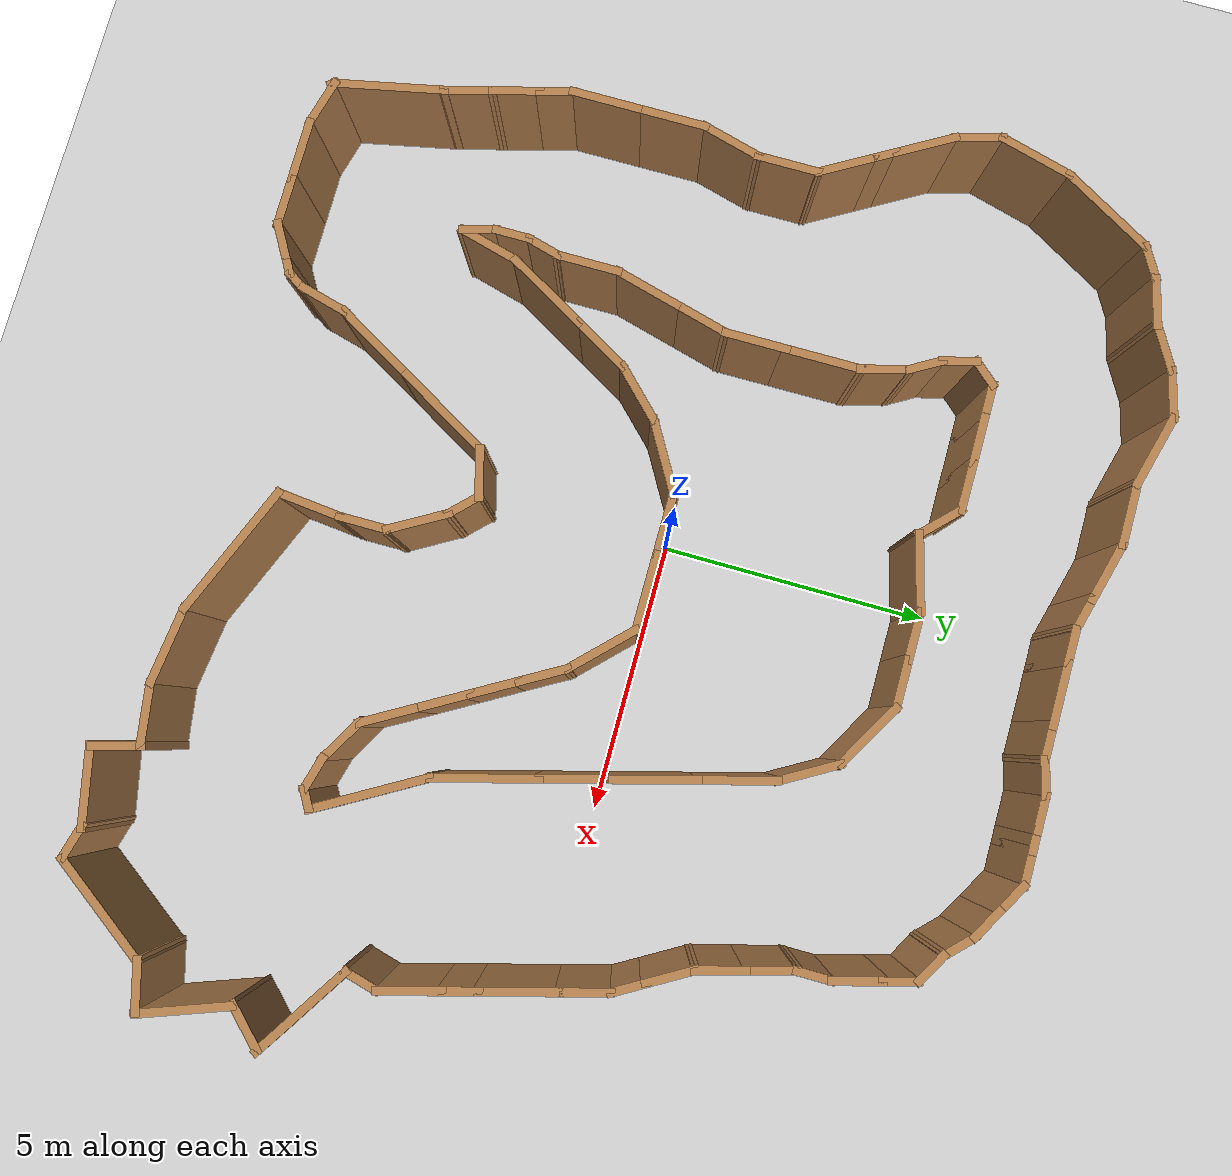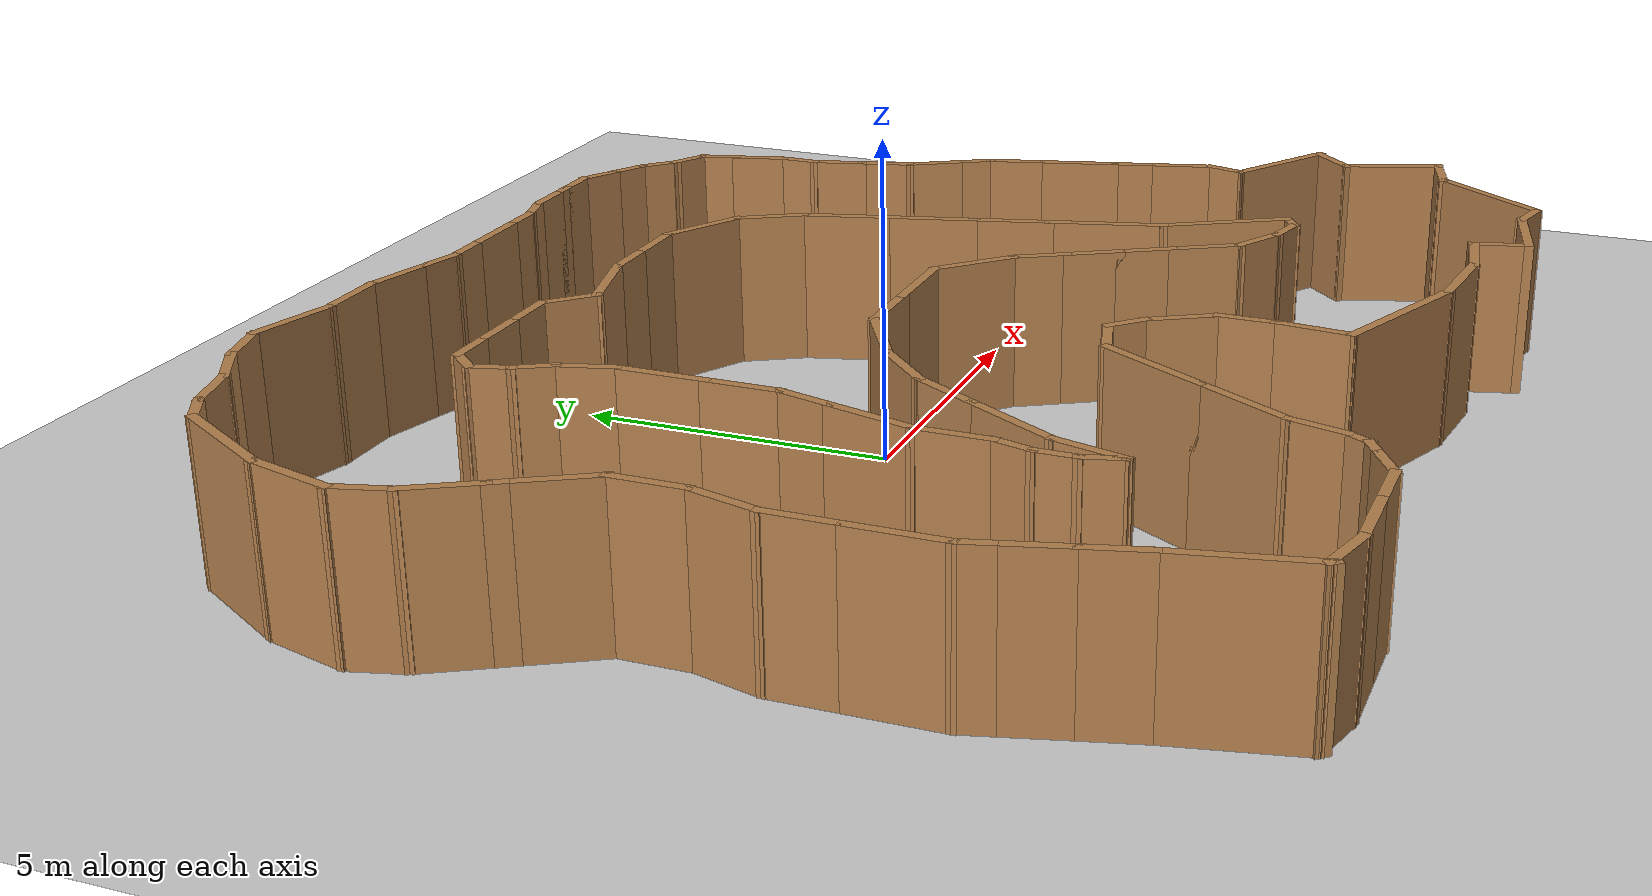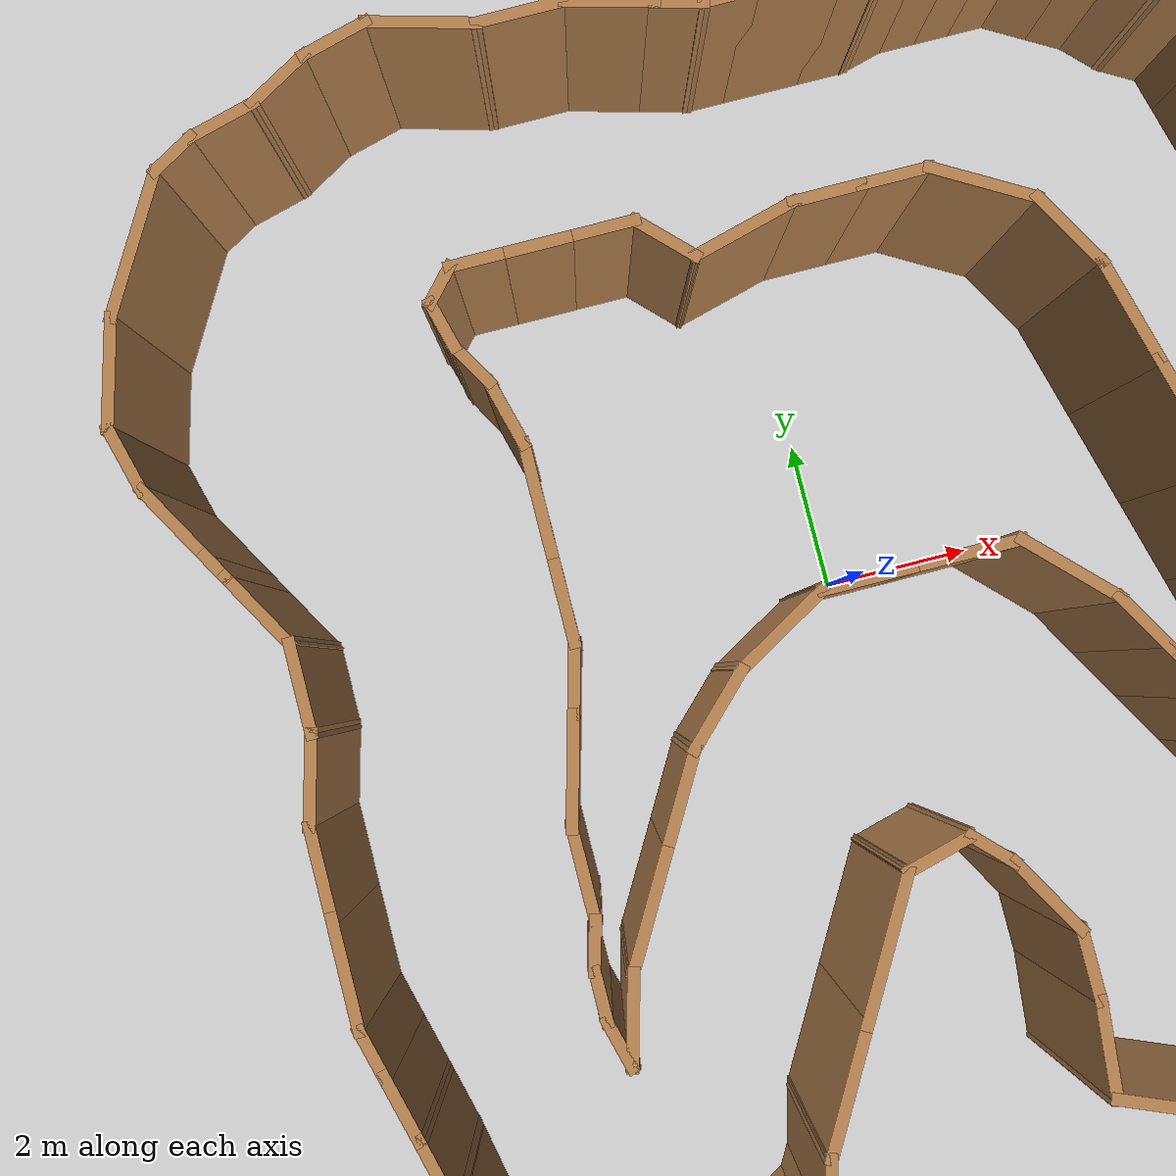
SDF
<sdf version="1.7">
 <world name="default">
  <light name="sun" type="directional">
   <pose>0 0 10 0 -0 0</pose>
   <diffuse>0.8 0.8 0.8 1</diffuse>
   <specular>0.2 0.2 0.2 1</specular>
   <attenuation>
    <range>1000</range>
    <constant>0.9</constant>
    <linear>0.01</linear>
    <quadratic>0.001</quadratic>
   </attenuation>
   <direction>-0.5 0.1 -0.9</direction>
   <spot><inner_angle>0</inner_angle><outer_angle>0</outer_angle><falloff>0</falloff></spot>
  </light>
  <model name="ground_plane">
   <static>1</static>
   <link name="link">
    <collision name="collision">
     <geometry><plane><normal>0 0 1</normal><size>100 100</size></plane></geometry>
     <surface><friction><ode><mu>100</mu><mu2>50</mu2></ode></friction></surface>
    </collision>
    <visual name="visual">
     <cast_shadows>0</cast_shadows>
     <geometry><plane><normal>0 0 1</normal><size>100 100</size></plane></geometry>
     <material>
      <script><uri>file://media/materials/scripts/gazebo.material</uri><name>Gazebo/Grey</name></script>
     </material>
    </visual>
   </link>
  </model>
  <gravity>0 0 -9.8</gravity>
  <magnetic_field>6e-06 2.3e-05 -4.2e-05</magnetic_field>
  <atmosphere type="adiabatic"/>
  <physics type="ode">
   <max_step_size>0.001</max_step_size>
   <real_time_factor>1</real_time_factor>
   <real_time_update_rate>1000</real_time_update_rate>
  </physics>
  <scene><ambient>0.4 0.4 0.4 1</ambient><background>0.7 0.7 0.7 1</background><shadows>1</shadows></scene>
  <audio><device>default</device></audio>
  <spherical_coordinates>
   <surface_model>EARTH_WGS84</surface_model>
   <latitude_deg>0</latitude_deg>
   <longitude_deg>0</longitude_deg>
   <elevation>0</elevation>
   <heading_deg>0</heading_deg>
  </spherical_coordinates>
  <model name="m-shape-circle">
   <pose>0.902463 -0.279625 0 0 -0 0</pose>
   <link name="Wall_10">
    <collision name="Wall_10_Collision">
     <geometry><box><size>0.75 0.15 2.5</size></box></geometry>
     <pose>0 0 1.25 0 -0 0</pose>
    </collision>
    <visual name="Wall_10_Visual">
     <pose>0 0 1.25 0 -0 0</pose>
     <geometry><box><size>0.75 0.15 2.5</size></box></geometry>
     <material>
      <script><uri>file://media/materials/scripts/gazebo.material</uri><name>Gazebo/Wood</name></script>
      <ambient>1 1 1 1</ambient>
     </material>
     <meta><layer>0</layer></meta>
    </visual>
    <pose>-8.04587 -3.77192 0 0 -0 1.8326</pose>
   </link>
   <link name="Wall_100">
    <collision name="Wall_100_Collision">
     <geometry><box><size>1 0.15 2.5</size></box></geometry>
     <pose>0 0 1.25 0 -0 0</pose>
    </collision>
    <visual name="Wall_100_Visual">
     <pose>0 0 1.25 0 -0 0</pose>
     <geometry><box><size>1 0.15 2.5</size></box></geometry>
     <material>
      <script><uri>file://media/materials/scripts/gazebo.material</uri><name>Gazebo/Wood</name></script>
      <ambient>1 1 1 1</ambient>
     </material>
     <meta><layer>0</layer></meta>
    </visual>
    <pose>0.581193 4.79872 0 0 -0 0</pose>
   </link>
   <link name="Wall_101">
    <collision name="Wall_101_Collision">
     <geometry><box><size>1.5 0.15 2.5</size></box></geometry>
     <pose>0 0 1.25 0 -0 0</pose>
    </collision>
    <visual name="Wall_101_Visual">
     <pose>0 0 1.25 0 -0 0</pose>
     <geometry><box><size>1.5 0.15 2.5</size></box></geometry>
     <material>
      <script><uri>file://media/materials/scripts/gazebo.material</uri><name>Gazebo/Wood</name></script>
      <ambient>1 1 1 1</ambient>
     </material>
     <meta><layer>0</layer></meta>
    </visual>
    <pose>1.59076 4.46122 0 0 -0 -0.523599</pose>
   </link>
   <link name="Wall_102">
    <collision name="Wall_102_Collision">
     <geometry><box><size>1.25 0.15 2.5</size></box></geometry>
     <pose>0 0 1.25 0 -0 0</pose>
    </collision>
    <visual name="Wall_102_Visual">
     <pose>0 0 1.25 0 -0 0</pose>
     <geometry><box><size>1.25 0.15 2.5</size></box></geometry>
     <material>
      <script><uri>file://media/materials/scripts/gazebo.material</uri><name>Gazebo/Wood</name></script>
      <ambient>1 1 1 1</ambient>
     </material>
     <meta><layer>0</layer></meta>
    </visual>
    <pose>2.45033 3.6474 0 0 -0 -1.0472</pose>
   </link>
   <link name="Wall_103">
    <collision name="Wall_103_Collision">
     <geometry><box><size>1.5 0.15 2.5</size></box></geometry>
     <pose>0 0 1.25 0 -0 0</pose>
    </collision>
    <visual name="Wall_103_Visual">
     <pose>0 0 1.25 0 -0 0</pose>
     <geometry><box><size>1.5 0.15 2.5</size></box></geometry>
     <material>
      <script><uri>file://media/materials/scripts/gazebo.material</uri><name>Gazebo/Wood</name></script>
      <ambient>1 1 1 1</ambient>
     </material>
     <meta><layer>0</layer></meta>
    </visual>
    <pose>2.90003 2.51909 0 0 -0 -1.309</pose>
   </link>
   <link name="Wall_104">
    <collision name="Wall_104_Collision">
     <geometry><box><size>1.75 0.15 2.5</size></box></geometry>
     <pose>0 0 1.25 0 -0 0</pose>
    </collision>
    <visual name="Wall_104_Visual">
     <pose>0 0 1.25 0 -0 0</pose>
     <geometry><box><size>1.75 0.15 2.5</size></box></geometry>
     <material>
      <script><uri>file://media/materials/scripts/gazebo.material</uri><name>Gazebo/Wood</name></script>
      <ambient>1 1 1 1</ambient>
     </material>
     <meta><layer>0</layer></meta>
    </visual>
    <pose>3.28179 1.09435 0 0 -0 -1.309</pose>
   </link>
   <link name="Wall_105">
    <collision name="Wall_105_Collision">
     <geometry><box><size>1.25 0.15 2.5</size></box></geometry>
     <pose>0 0 1.25 0 -0 0</pose>
    </collision>
    <visual name="Wall_105_Visual">
     <pose>0 0 1.25 0 -0 0</pose>
     <geometry><box><size>1.25 0.15 2.5</size></box></geometry>
     <material>
      <script><uri>file://media/materials/scripts/gazebo.material</uri><name>Gazebo/Wood</name></script>
      <ambient>1 1 1 1</ambient>
     </material>
     <meta><layer>0</layer></meta>
    </visual>
    <pose>3.63119 -0.209651 0 0 -0 -1.309</pose>
   </link>
   <link name="Wall_106">
    <collision name="Wall_106_Collision">
     <geometry><box><size>2 0.15 2.5</size></box></geometry>
     <pose>0 0 1.25 0 -0 0</pose>
    </collision>
    <visual name="Wall_106_Visual">
     <pose>0 0 1.25 0 -0 0</pose>
     <geometry><box><size>2 0.15 2.5</size></box></geometry>
     <material>
      <script><uri>file://media/materials/scripts/gazebo.material</uri><name>Gazebo/Wood</name></script>
      <ambient>1 1 1 1</ambient>
     </material>
     <meta><layer>0</layer></meta>
    </visual>
    <pose>4.01295 -1.63439 0 0 -0 -1.309</pose>
   </link>
   <link name="Wall_107">
    <collision name="Wall_107_Collision">
     <geometry><box><size>2.25 0.15 2.5</size></box></geometry>
     <pose>0 0 1.25 0 -0 0</pose>
    </collision>
    <visual name="Wall_107_Visual">
     <pose>0 0 1.25 0 -0 0</pose>
     <geometry><box><size>2.25 0.15 2.5</size></box></geometry>
     <material>
      <script><uri>file://media/materials/scripts/gazebo.material</uri><name>Gazebo/Wood</name></script>
      <ambient>1 1 1 1</ambient>
     </material>
     <meta><layer>0</layer></meta>
    </visual>
    <pose>4.77736 -3.4372 0 0 -0 -1.0472</pose>
   </link>
   <link name="Wall_108">
    <collision name="Wall_108_Collision">
     <geometry><box><size>0.5 0.15 2.5</size></box></geometry>
     <pose>0 0 1.25 0 -0 0</pose>
    </collision>
    <visual name="Wall_108_Visual">
     <pose>0 0 1.25 0 -0 0</pose>
     <geometry><box><size>0.5 0.15 2.5</size></box></geometry>
     <material>
      <script><uri>file://media/materials/scripts/gazebo.material</uri><name>Gazebo/Wood</name></script>
      <ambient>1 1 1 1</ambient>
     </material>
     <meta><layer>0</layer></meta>
    </visual>
    <pose>5.15081 -4.43403 0 0 -0 -2.61799</pose>
   </link>
   <link name="Wall_109">
    <collision name="Wall_109_Collision">
     <geometry><box><size>0.75 0.15 2.5</size></box></geometry>
     <pose>0 0 1.25 0 -0 0</pose>
    </collision>
    <visual name="Wall_109_Visual">
     <pose>0 0 1.25 0 -0 0</pose>
     <geometry><box><size>0.75 0.15 2.5</size></box></geometry>
     <material>
      <script><uri>file://media/materials/scripts/gazebo.material</uri><name>Gazebo/Wood</name></script>
      <ambient>1 1 1 1</ambient>
     </material>
     <meta><layer>0</layer></meta>
    </visual>
    <pose>4.70947 -4.44388 0 0 -0 2.87979</pose>
   </link>
   <link name="Wall_11">
    <collision name="Wall_11_Collision">
     <geometry><box><size>1.5 0.15 2.5</size></box></geometry>
     <pose>0 0 1.25 0 -0 0</pose>
    </collision>
    <visual name="Wall_11_Visual">
     <pose>0 0 1.25 0 -0 0</pose>
     <geometry><box><size>1.5 0.15 2.5</size></box></geometry>
     <material>
      <script><uri>file://media/materials/scripts/gazebo.material</uri><name>Gazebo/Wood</name></script>
      <ambient>1 1 1 1</ambient>
     </material>
     <meta><layer>0</layer></meta>
    </visual>
    <pose>-8.12351 -2.80714 0 0 -0 1.5708</pose>
   </link>
   <link name="Wall_110">
    <collision name="Wall_110_Collision">
     <geometry><box><size>1 0.15 2.5</size></box></geometry>
     <pose>0 0 1.25 0 -0 0</pose>
    </collision>
    <visual name="Wall_110_Visual">
     <pose>0 0 1.25 0 -0 0</pose>
     <geometry><box><size>1 0.15 2.5</size></box></geometry>
     <material>
      <script><uri>file://media/materials/scripts/gazebo.material</uri><name>Gazebo/Wood</name></script>
      <ambient>1 1 1 1</ambient>
     </material>
     <meta><layer>0</layer></meta>
    </visual>
    <pose>4.05163 -4.15374 0 0 -0 2.61799</pose>
   </link>
   <link name="Wall_111">
    <collision name="Wall_111_Collision">
     <geometry><box><size>1.25 0.15 2.5</size></box></geometry>
     <pose>0 0 1.25 0 -0 0</pose>
    </collision>
    <visual name="Wall_111_Visual">
     <pose>0 0 1.25 0 -0 0</pose>
     <geometry><box><size>1.25 0.15 2.5</size></box></geometry>
     <material>
      <script><uri>file://media/materials/scripts/gazebo.material</uri><name>Gazebo/Wood</name></script>
      <ambient>1 1 1 1</ambient>
     </material>
     <meta><layer>0</layer></meta>
    </visual>
    <pose>3.40857 -3.46492 0 0 -0 2.0944</pose>
   </link>
   <link name="Wall_112">
    <collision name="Wall_112_Collision">
     <geometry><box><size>1 0.15 2.5</size></box></geometry>
     <pose>0 0 1.25 0 -0 0</pose>
    </collision>
    <visual name="Wall_112_Visual">
     <pose>0 0 1.25 0 -0 0</pose>
     <geometry><box><size>1 0.15 2.5</size></box></geometry>
     <material>
      <script><uri>file://media/materials/scripts/gazebo.material</uri><name>Gazebo/Wood</name></script>
      <ambient>1 1 1 1</ambient>
     </material>
     <meta><layer>0</layer></meta>
    </visual>
    <pose>2.92107 -2.62055 0 0 -0 2.0944</pose>
   </link>
   <link name="Wall_113">
    <collision name="Wall_113_Collision">
     <geometry><box><size>1 0.15 2.5</size></box></geometry>
     <pose>0 0 1.25 0 -0 0</pose>
    </collision>
    <visual name="Wall_113_Visual">
     <pose>0 0 1.25 0 -0 0</pose>
     <geometry><box><size>1 0.15 2.5</size></box></geometry>
     <material>
      <script><uri>file://media/materials/scripts/gazebo.material</uri><name>Gazebo/Wood</name></script>
      <ambient>1 1 1 1</ambient>
     </material>
     <meta><layer>0</layer></meta>
    </visual>
    <pose>2.49607 -1.88443 0 0 -0 2.0944</pose>
   </link>
   <link name="Wall_114">
    <collision name="Wall_114_Collision">
     <geometry><box><size>1 0.15 2.5</size></box></geometry>
     <pose>0 0 1.25 0 -0 0</pose>
    </collision>
    <visual name="Wall_114_Visual">
     <pose>0 0 1.25 0 -0 0</pose>
     <geometry><box><size>1 0.15 2.5</size></box></geometry>
     <material>
      <script><uri>file://media/materials/scripts/gazebo.material</uri><name>Gazebo/Wood</name></script>
      <ambient>1 1 1 1</ambient>
     </material>
     <meta><layer>0</layer></meta>
    </visual>
    <pose>2.07107 -1.1483 0 0 -0 2.0944</pose>
   </link>
   <link name="Wall_115">
    <collision name="Wall_115_Collision">
     <geometry><box><size>1.5 0.15 2.5</size></box></geometry>
     <pose>0 0 1.25 0 -0 0</pose>
    </collision>
    <visual name="Wall_115_Visual">
     <pose>0 0 1.25 0 -0 0</pose>
     <geometry><box><size>1.5 0.15 2.5</size></box></geometry>
     <material>
      <script><uri>file://media/materials/scripts/gazebo.material</uri><name>Gazebo/Wood</name></script>
      <ambient>1 1 1 1</ambient>
     </material>
     <meta><layer>0</layer></meta>
    </visual>
    <pose>1.38128 -0.302945 0 0 -0 2.35619</pose>
   </link>
   <link name="Wall_116">
    <collision name="Wall_116_Collision">
     <geometry><box><size>1.5 0.15 2.5</size></box></geometry>
     <pose>0 0 1.25 0 -0 0</pose>
    </collision>
    <visual name="Wall_116_Visual">
     <pose>0 0 1.25 0 -0 0</pose>
     <geometry><box><size>1.5 0.15 2.5</size></box></geometry>
     <material>
      <script><uri>file://media/materials/scripts/gazebo.material</uri><name>Gazebo/Wood</name></script>
      <ambient>1 1 1 1</ambient>
     </material>
     <meta><layer>0</layer></meta>
    </visual>
    <pose>0.228979 0.174352 0 0 -0 3.14159</pose>
   </link>
   <link name="Wall_117">
    <collision name="Wall_117_Collision">
     <geometry><box><size>1.25 0.15 2.5</size></box></geometry>
     <pose>0 0 1.25 0 -0 0</pose>
    </collision>
    <visual name="Wall_117_Visual">
     <pose>0 0 1.25 0 -0 0</pose>
     <geometry><box><size>1.25 0.15 2.5</size></box></geometry>
     <material>
      <script><uri>file://media/materials/scripts/gazebo.material</uri><name>Gazebo/Wood</name></script>
      <ambient>1 1 1 1</ambient>
     </material>
     <meta><layer>0</layer></meta>
    </visual>
    <pose>-0.996021 0.174352 0 0 -0 3.14159</pose>
   </link>
   <link name="Wall_118">
    <collision name="Wall_118_Collision">
     <geometry><box><size>1.5 0.15 2.5</size></box></geometry>
     <pose>0 0 1.25 0 -0 0</pose>
    </collision>
    <visual name="Wall_118_Visual">
     <pose>0 0 1.25 0 -0 0</pose>
     <geometry><box><size>1.5 0.15 2.5</size></box></geometry>
     <material>
      <script><uri>file://media/materials/scripts/gazebo.material</uri><name>Gazebo/Wood</name></script>
      <ambient>1 1 1 1</ambient>
     </material>
     <meta><layer>0</layer></meta>
    </visual>
    <pose>-2.13059 -0.163148 0 0 -0 -2.61799</pose>
   </link>
   <link name="Wall_119">
    <collision name="Wall_119_Collision">
     <geometry><box><size>1.25 0.15 2.5</size></box></geometry>
     <pose>0 0 1.25 0 -0 0</pose>
    </collision>
    <visual name="Wall_119_Visual">
     <pose>0 0 1.25 0 -0 0</pose>
     <geometry><box><size>1.25 0.15 2.5</size></box></geometry>
     <material>
      <script><uri>file://media/materials/scripts/gazebo.material</uri><name>Gazebo/Wood</name></script>
      <ambient>1 1 1 1</ambient>
     </material>
     <meta><layer>0</layer></meta>
    </visual>
    <pose>-3.10406 -0.889557 0 0 -0 -2.35619</pose>
   </link>
   <link name="Wall_12">
    <collision name="Wall_12_Collision">
     <geometry><box><size>1.25 0.15 2.5</size></box></geometry>
     <pose>0 0 1.25 0 -0 0</pose>
    </collision>
    <visual name="Wall_12_Visual">
     <pose>0 0 1.25 0 -0 0</pose>
     <geometry><box><size>1.25 0.15 2.5</size></box></geometry>
     <material>
      <script><uri>file://media/materials/scripts/gazebo.material</uri><name>Gazebo/Wood</name></script>
      <ambient>1 1 1 1</ambient>
     </material>
     <meta><layer>0</layer></meta>
    </visual>
    <pose>-8.12351 -1.58214 0 0 -0 1.5708</pose>
   </link>
   <link name="Wall_120">
    <collision name="Wall_120_Collision">
     <geometry><box><size>1.25 0.15 2.5</size></box></geometry>
     <pose>0 0 1.25 0 -0 0</pose>
    </collision>
    <visual name="Wall_120_Visual">
     <pose>0 0 1.25 0 -0 0</pose>
     <geometry><box><size>1.25 0.15 2.5</size></box></geometry>
     <material>
      <script><uri>file://media/materials/scripts/gazebo.material</uri><name>Gazebo/Wood</name></script>
      <ambient>1 1 1 1</ambient>
     </material>
     <meta><layer>0</layer></meta>
    </visual>
    <pose>-3.76797 -1.75478 0 0 -0 -2.0944</pose>
   </link>
   <link name="Wall_121">
    <collision name="Wall_121_Collision">
     <geometry><box><size>1.75 0.15 2.5</size></box></geometry>
     <pose>0 0 1.25 0 -0 0</pose>
    </collision>
    <visual name="Wall_121_Visual">
     <pose>0 0 1.25 0 -0 0</pose>
     <geometry><box><size>1.75 0.15 2.5</size></box></geometry>
     <material>
      <script><uri>file://media/materials/scripts/gazebo.material</uri><name>Gazebo/Wood</name></script>
      <ambient>1 1 1 1</ambient>
     </material>
     <meta><layer>0</layer></meta>
    </visual>
    <pose>-4.44297 -2.92391 0 0 -0 -2.0944</pose>
   </link>
   <link name="Wall_122">
    <collision name="Wall_122_Collision">
     <geometry><box><size>1.25 0.15 2.5</size></box></geometry>
     <pose>0 0 1.25 0 -0 0</pose>
    </collision>
    <visual name="Wall_122_Visual">
     <pose>0 0 1.25 0 -0 0</pose>
     <geometry><box><size>1.25 0.15 2.5</size></box></geometry>
     <material>
      <script><uri>file://media/materials/scripts/gazebo.material</uri><name>Gazebo/Wood</name></script>
      <ambient>1 1 1 1</ambient>
     </material>
     <meta><layer>0</layer></meta>
    </visual>
    <pose>-4.98532 -4.14799 0 0 -0 -1.8326</pose>
   </link>
   <link name="Wall_123">
    <collision name="Wall_123_Collision">
     <geometry><box><size>0.75 0.15 2.5</size></box></geometry>
     <pose>0 0 1.25 0 -0 0</pose>
    </collision>
    <visual name="Wall_123_Visual">
     <pose>0 0 1.25 0 -0 0</pose>
     <geometry><box><size>0.75 0.15 2.5</size></box></geometry>
     <material>
      <script><uri>file://media/materials/scripts/gazebo.material</uri><name>Gazebo/Wood</name></script>
      <ambient>1 1 1 1</ambient>
     </material>
     <meta><layer>0</layer></meta>
    </visual>
    <pose>-5.20532 -4.38948 0 0 -0 1.8326</pose>
   </link>
   <link name="Wall_124">
    <collision name="Wall_124_Collision">
     <geometry><box><size>0.75 0.15 2.5</size></box></geometry>
     <pose>0 0 1.25 0 -0 0</pose>
    </collision>
    <visual name="Wall_124_Visual">
     <pose>0 0 1.25 0 -0 0</pose>
     <geometry><box><size>0.75 0.15 2.5</size></box></geometry>
     <material>
      <script><uri>file://media/materials/scripts/gazebo.material</uri><name>Gazebo/Wood</name></script>
      <ambient>1 1 1 1</ambient>
     </material>
     <meta><layer>0</layer></meta>
    </visual>
    <pose>-5.28296 -3.7997 0 0 -0 1.5708</pose>
   </link>
   <link name="Wall_125">
    <collision name="Wall_125_Collision">
     <geometry><box><size>0.75 0.15 2.5</size></box></geometry>
     <pose>0 0 1.25 0 -0 0</pose>
    </collision>
    <visual name="Wall_125_Visual">
     <pose>0 0 1.25 0 -0 0</pose>
     <geometry><box><size>0.75 0.15 2.5</size></box></geometry>
     <material>
      <script><uri>file://media/materials/scripts/gazebo.material</uri><name>Gazebo/Wood</name></script>
      <ambient>1 1 1 1</ambient>
     </material>
     <meta><layer>0</layer></meta>
    </visual>
    <pose>-5.20532 -3.20992 0 0 -0 1.309</pose>
   </link>
   <link name="Wall_126">
    <collision name="Wall_126_Collision">
     <geometry><box><size>1.25 0.15 2.5</size></box></geometry>
     <pose>0 0 1.25 0 -0 0</pose>
    </collision>
    <visual name="Wall_126_Visual">
     <pose>0 0 1.25 0 -0 0</pose>
     <geometry><box><size>1.25 0.15 2.5</size></box></geometry>
     <material>
      <script><uri>file://media/materials/scripts/gazebo.material</uri><name>Gazebo/Wood</name></script>
      <ambient>1 1 1 1</ambient>
     </material>
     <meta><layer>0</layer></meta>
    </visual>
    <pose>-5.12767 -2.37014 0 0 -0 1.5708</pose>
   </link>
   <link name="Wall_127">
    <collision name="Wall_127_Collision">
     <geometry><box><size>1.5 0.15 2.5</size></box></geometry>
     <pose>0 0 1.25 0 -0 0</pose>
    </collision>
    <visual name="Wall_127_Visual">
     <pose>0 0 1.25 0 -0 0</pose>
     <geometry><box><size>1.5 0.15 2.5</size></box></geometry>
     <material>
      <script><uri>file://media/materials/scripts/gazebo.material</uri><name>Gazebo/Wood</name></script>
      <ambient>1 1 1 1</ambient>
     </material>
     <meta><layer>0</layer></meta>
    </visual>
    <pose>-4.95297 -1.16814 0 0 -0 1.309</pose>
   </link>
   <link name="Wall_128">
    <collision name="Wall_128_Collision">
     <geometry><box><size>1 0.15 2.5</size></box></geometry>
     <pose>0 0 1.25 0 -0 0</pose>
    </collision>
    <visual name="Wall_128_Visual">
     <pose>0 0 1.25 0 -0 0</pose>
     <geometry><box><size>1 0.15 2.5</size></box></geometry>
     <material>
      <script><uri>file://media/materials/scripts/gazebo.material</uri><name>Gazebo/Wood</name></script>
      <ambient>1 1 1 1</ambient>
     </material>
     <meta><layer>0</layer></meta>
    </visual>
    <pose>-4.66827 -0.105623 0 0 -0 1.309</pose>
   </link>
   <link name="Wall_129">
    <collision name="Wall_129_Collision">
     <geometry><box><size>1.25 0.15 2.5</size></box></geometry>
     <pose>0 0 1.25 0 -0 0</pose>
    </collision>
    <visual name="Wall_129_Visual">
     <pose>0 0 1.25 0 -0 0</pose>
     <geometry><box><size>1.25 0.15 2.5</size></box></geometry>
     <material>
      <script><uri>file://media/materials/scripts/gazebo.material</uri><name>Gazebo/Wood</name></script>
      <ambient>1 1 1 1</ambient>
     </material>
     <meta><layer>0</layer></meta>
    </visual>
    <pose>-4.55827 0.854895 0 0 -0 1.5708</pose>
   </link>
   <link name="Wall_13">
    <collision name="Wall_13_Collision">
     <geometry><box><size>1.25 0.15 2.5</size></box></geometry>
     <pose>0 0 1.25 0 -0 0</pose>
    </collision>
    <visual name="Wall_13_Visual">
     <pose>0 0 1.25 0 -0 0</pose>
     <geometry><box><size>1.25 0.15 2.5</size></box></geometry>
     <material>
      <script><uri>file://media/materials/scripts/gazebo.material</uri><name>Gazebo/Wood</name></script>
      <ambient>1 1 1 1</ambient>
     </material>
     <meta><layer>0</layer></meta>
    </visual>
    <pose>-7.98116 -0.500884 0 0 -0 1.309</pose>
   </link>
   <link name="Wall_130">
    <collision name="Wall_130_Collision">
     <geometry><box><size>1.5 0.15 2.5</size></box></geometry>
     <pose>0 0 1.25 0 -0 0</pose>
    </collision>
    <visual name="Wall_130_Visual">
     <pose>0 0 1.25 0 -0 0</pose>
     <geometry><box><size>1.5 0.15 2.5</size></box></geometry>
     <material>
      <script><uri>file://media/materials/scripts/gazebo.material</uri><name>Gazebo/Wood</name></script>
      <ambient>1 1 1 1</ambient>
     </material>
     <meta><layer>0</layer></meta>
    </visual>
    <pose>-4.55827 2.0799 0 0 -0 1.5708</pose>
   </link>
   <link name="Wall_131">
    <collision name="Wall_131_Collision">
     <geometry><box><size>1 0.15 2.5</size></box></geometry>
     <pose>0 0 1.25 0 -0 0</pose>
    </collision>
    <visual name="Wall_131_Visual">
     <pose>0 0 1.25 0 -0 0</pose>
     <geometry><box><size>1 0.15 2.5</size></box></geometry>
     <material>
      <script><uri>file://media/materials/scripts/gazebo.material</uri><name>Gazebo/Wood</name></script>
      <ambient>1 1 1 1</ambient>
     </material>
     <meta><layer>0</layer></meta>
    </visual>
    <pose>-4.66827 3.16541 0 0 -0 1.8326</pose>
   </link>
   <link name="Wall_132">
    <collision name="Wall_132_Collision">
     <geometry><box><size>0.75 0.15 2.5</size></box></geometry>
     <pose>0 0 1.25 0 -0 0</pose>
    </collision>
    <visual name="Wall_132_Visual">
     <pose>0 0 1.25 0 -0 0</pose>
     <geometry><box><size>0.75 0.15 2.5</size></box></geometry>
     <material>
      <script><uri>file://media/materials/scripts/gazebo.material</uri><name>Gazebo/Wood</name></script>
      <ambient>1 1 1 1</ambient>
     </material>
     <meta><layer>0</layer></meta>
    </visual>
    <pose>-4.92827 3.83574 0 0 -0 2.0944</pose>
   </link>
   <link name="Wall_133">
    <collision name="Wall_133_Collision">
     <geometry><box><size>0.75 0.15 2.5</size></box></geometry>
     <pose>0 0 1.25 0 -0 0</pose>
    </collision>
    <visual name="Wall_133_Visual">
     <pose>0 0 1.25 0 -0 0</pose>
     <geometry><box><size>0.75 0.15 2.5</size></box></geometry>
     <material>
      <script><uri>file://media/materials/scripts/gazebo.material</uri><name>Gazebo/Wood</name></script>
      <ambient>1 1 1 1</ambient>
     </material>
     <meta><layer>0</layer></meta>
    </visual>
    <pose>-5.15591 4.38532 0 0 -0 1.8326</pose>
   </link>
   <link name="Wall_134">
    <collision name="Wall_134_Collision">
     <geometry><box><size>0.652836 0.15 2.5</size></box></geometry>
     <pose>0 0 1.25 0 -0 0</pose>
    </collision>
    <visual name="Wall_134_Visual">
     <pose>0 0 1.25 0 -0 0</pose>
     <geometry><box><size>0.652836 0.15 2.5</size></box></geometry>
     <material>
      <script><uri>file://media/materials/scripts/gazebo.material</uri><name>Gazebo/Wood</name></script>
      <ambient>1 1 1 1</ambient>
     </material>
     <meta><layer>0</layer></meta>
    </visual>
    <pose>-5.0662 4.86273 0 0 -0 0.842435</pose>
   </link>
   <link name="Wall_14">
    <collision name="Wall_14_Collision">
     <geometry><box><size>1.25 0.15 2.5</size></box></geometry>
     <pose>0 0 1.25 0 -0 0</pose>
    </collision>
    <visual name="Wall_14_Visual">
     <pose>0 0 1.25 0 -0 0</pose>
     <geometry><box><size>1.25 0.15 2.5</size></box></geometry>
     <material>
      <script><uri>file://media/materials/scripts/gazebo.material</uri><name>Gazebo/Wood</name></script>
      <ambient>1 1 1 1</ambient>
     </material>
     <meta><layer>0</layer></meta>
    </visual>
    <pose>-7.83881 0.580375 0 0 -0 1.5708</pose>
   </link>
   <link name="Wall_15">
    <collision name="Wall_15_Collision">
     <geometry><box><size>1.25 0.15 2.5</size></box></geometry>
     <pose>0 0 1.25 0 -0 0</pose>
    </collision>
    <visual name="Wall_15_Visual">
     <pose>0 0 1.25 0 -0 0</pose>
     <geometry><box><size>1.25 0.15 2.5</size></box></geometry>
     <material>
      <script><uri>file://media/materials/scripts/gazebo.material</uri><name>Gazebo/Wood</name></script>
      <ambient>1 1 1 1</ambient>
     </material>
     <meta><layer>0</layer></meta>
    </visual>
    <pose>-8.11381 1.60669 0 0 -0 2.0944</pose>
   </link>
   <link name="Wall_16">
    <collision name="Wall_16_Collision">
     <geometry><box><size>0.5 0.15 2.5</size></box></geometry>
     <pose>0 0 1.25 0 -0 0</pose>
    </collision>
    <visual name="Wall_16_Visual">
     <pose>0 0 1.25 0 -0 0</pose>
     <geometry><box><size>0.5 0.15 2.5</size></box></geometry>
     <material>
      <script><uri>file://media/materials/scripts/gazebo.material</uri><name>Gazebo/Wood</name></script>
      <ambient>1 1 1 1</ambient>
     </material>
     <meta><layer>0</layer></meta>
    </visual>
    <pose>-8.47631 2.23456 0 0 -0 2.0944</pose>
   </link>
   <link name="Wall_17">
    <collision name="Wall_17_Collision">
     <geometry><box><size>1.25 0.15 2.5</size></box></geometry>
     <pose>0 0 1.25 0 -0 0</pose>
    </collision>
    <visual name="Wall_17_Visual">
     <pose>0 0 1.25 0 -0 0</pose>
     <geometry><box><size>1.25 0.15 2.5</size></box></geometry>
     <material>
      <script><uri>file://media/materials/scripts/gazebo.material</uri><name>Gazebo/Wood</name></script>
      <ambient>1 1 1 1</ambient>
     </material>
     <meta><layer>0</layer></meta>
    </visual>
    <pose>-8.83881 2.86243 0 0 -0 2.0944</pose>
   </link>
   <link name="Wall_18">
    <collision name="Wall_18_Collision">
     <geometry><box><size>1 0.15 2.5</size></box></geometry>
     <pose>0 0 1.25 0 -0 0</pose>
    </collision>
    <visual name="Wall_18_Visual">
     <pose>0 0 1.25 0 -0 0</pose>
     <geometry><box><size>1 0.15 2.5</size></box></geometry>
     <material>
      <script><uri>file://media/materials/scripts/gazebo.material</uri><name>Gazebo/Wood</name></script>
      <ambient>1 1 1 1</ambient>
     </material>
     <meta><layer>0</layer></meta>
    </visual>
    <pose>-9.22381 3.74926 0 0 -0 1.8326</pose>
   </link>
   <link name="Wall_19">
    <collision name="Wall_19_Collision">
     <geometry><box><size>1.5 0.15 2.5</size></box></geometry>
     <pose>0 0 1.25 0 -0 0</pose>
    </collision>
    <visual name="Wall_19_Visual">
     <pose>0 0 1.25 0 -0 0</pose>
     <geometry><box><size>1.5 0.15 2.5</size></box></geometry>
     <material>
      <script><uri>file://media/materials/scripts/gazebo.material</uri><name>Gazebo/Wood</name></script>
      <ambient>1 1 1 1</ambient>
     </material>
     <meta><layer>0</layer></meta>
    </visual>
    <pose>-9.15911 4.81178 0 0 -0 1.309</pose>
   </link>
   <link name="Wall_20">
    <collision name="Wall_20_Collision">
     <geometry><box><size>2 0.15 2.5</size></box></geometry>
     <pose>0 0 1.25 0 -0 0</pose>
    </collision>
    <visual name="Wall_20_Visual">
     <pose>0 0 1.25 0 -0 0</pose>
     <geometry><box><size>2 0.15 2.5</size></box></geometry>
     <material>
      <script><uri>file://media/materials/scripts/gazebo.material</uri><name>Gazebo/Wood</name></script>
      <ambient>1 1 1 1</ambient>
     </material>
     <meta><layer>0</layer></meta>
    </visual>
    <pose>-8.5219 6.26485 0 0 -0 1.0472</pose>
   </link>
   <link name="Wall_21">
    <collision name="Wall_21_Collision">
     <geometry><box><size>0.75 0.15 2.5</size></box></geometry>
     <pose>0 0 1.25 0 -0 0</pose>
    </collision>
    <visual name="Wall_21_Visual">
     <pose>0 0 1.25 0 -0 0</pose>
     <geometry><box><size>0.75 0.15 2.5</size></box></geometry>
     <material>
      <script><uri>file://media/materials/scripts/gazebo.material</uri><name>Gazebo/Wood</name></script>
      <ambient>1 1 1 1</ambient>
     </material>
     <meta><layer>0</layer></meta>
    </visual>
    <pose>-7.7996 7.21592 0 0 -0 0.523599</pose>
   </link>
   <link name="Wall_22">
    <collision name="Wall_22_Collision">
     <geometry><box><size>1 0.15 2.5</size></box></geometry>
     <pose>0 0 1.25 0 -0 0</pose>
    </collision>
    <visual name="Wall_22_Visual">
     <pose>0 0 1.25 0 -0 0</pose>
     <geometry><box><size>1 0.15 2.5</size></box></geometry>
     <material>
      <script><uri>file://media/materials/scripts/gazebo.material</uri><name>Gazebo/Wood</name></script>
      <ambient>1 1 1 1</ambient>
     </material>
     <meta><layer>0</layer></meta>
    </visual>
    <pose>-7.12927 7.47592 0 0 -0 0.261799</pose>
   </link>
   <link name="Wall_23">
    <collision name="Wall_23_Collision">
     <geometry><box><size>1 0.15 2.5</size></box></geometry>
     <pose>0 0 1.25 0 -0 0</pose>
    </collision>
    <visual name="Wall_23_Visual">
     <pose>0 0 1.25 0 -0 0</pose>
     <geometry><box><size>1 0.15 2.5</size></box></geometry>
     <material>
      <script><uri>file://media/materials/scripts/gazebo.material</uri><name>Gazebo/Wood</name></script>
      <ambient>1 1 1 1</ambient>
     </material>
     <meta><layer>0</layer></meta>
    </visual>
    <pose>-6.35069 7.79842 0 0 -0 0.523599</pose>
   </link>
   <link name="Wall_24">
    <collision name="Wall_24_Collision">
     <geometry><box><size>1 0.15 2.5</size></box></geometry>
     <pose>0 0 1.25 0 -0 0</pose>
    </collision>
    <visual name="Wall_24_Visual">
     <pose>0 0 1.25 0 -0 0</pose>
     <geometry><box><size>1 0.15 2.5</size></box></geometry>
     <material>
      <script><uri>file://media/materials/scripts/gazebo.material</uri><name>Gazebo/Wood</name></script>
      <ambient>1 1 1 1</ambient>
     </material>
     <meta><layer>0</layer></meta>
    </visual>
    <pose>-5.57211 8.12092 0 0 -0 0.261799</pose>
   </link>
   <link name="Wall_25">
    <collision name="Wall_25_Collision">
     <geometry><box><size>1.5 0.15 2.5</size></box></geometry>
     <pose>0 0 1.25 0 -0 0</pose>
    </collision>
    <visual name="Wall_25_Visual">
     <pose>0 0 1.25 0 -0 0</pose>
     <geometry><box><size>1.5 0.15 2.5</size></box></geometry>
     <material>
      <script><uri>file://media/materials/scripts/gazebo.material</uri><name>Gazebo/Wood</name></script>
      <ambient>1 1 1 1</ambient>
     </material>
     <meta><layer>0</layer></meta>
    </visual>
    <pose>-4.50959 8.05621 0 0 -0 -0.261799</pose>
   </link>
   <link name="Wall_26">
    <collision name="Wall_26_Collision">
     <geometry><box><size>1.25 0.15 2.5</size></box></geometry>
     <pose>0 0 1.25 0 -0 0</pose>
    </collision>
    <visual name="Wall_26_Visual">
     <pose>0 0 1.25 0 -0 0</pose>
     <geometry><box><size>1.25 0.15 2.5</size></box></geometry>
     <material>
      <script><uri>file://media/materials/scripts/gazebo.material</uri><name>Gazebo/Wood</name></script>
      <ambient>1 1 1 1</ambient>
     </material>
     <meta><layer>0</layer></meta>
    </visual>
    <pose>-3.30759 7.88151 0 0 -0 0</pose>
   </link>
   <link name="Wall_27">
    <collision name="Wall_27_Collision">
     <geometry><box><size>1.25 0.15 2.5</size></box></geometry>
     <pose>0 0 1.25 0 -0 0</pose>
    </collision>
    <visual name="Wall_27_Visual">
     <pose>0 0 1.25 0 -0 0</pose>
     <geometry><box><size>1.25 0.15 2.5</size></box></geometry>
     <material>
      <script><uri>file://media/materials/scripts/gazebo.material</uri><name>Gazebo/Wood</name></script>
      <ambient>1 1 1 1</ambient>
     </material>
     <meta><layer>0</layer></meta>
    </visual>
    <pose>-2.22634 7.73916 0 0 -0 -0.261799</pose>
   </link>
   <link name="Wall_28">
    <collision name="Wall_28_Collision">
     <geometry><box><size>0.75 0.15 2.5</size></box></geometry>
     <pose>0 0 1.25 0 -0 0</pose>
    </collision>
    <visual name="Wall_28_Visual">
     <pose>0 0 1.25 0 -0 0</pose>
     <geometry><box><size>0.75 0.15 2.5</size></box></geometry>
     <material>
      <script><uri>file://media/materials/scripts/gazebo.material</uri><name>Gazebo/Wood</name></script>
      <ambient>1 1 1 1</ambient>
     </material>
     <meta><layer>0</layer></meta>
    </visual>
    <pose>-1.4053 7.51916 0 0 -0 -0.261799</pose>
   </link>
   <link name="Wall_29">
    <collision name="Wall_29_Collision">
     <geometry><box><size>0.75 0.15 2.5</size></box></geometry>
     <pose>0 0 1.25 0 -0 0</pose>
    </collision>
    <visual name="Wall_29_Visual">
     <pose>0 0 1.25 0 -0 0</pose>
     <geometry><box><size>0.75 0.15 2.5</size></box></geometry>
     <material>
      <script><uri>file://media/materials/scripts/gazebo.material</uri><name>Gazebo/Wood</name></script>
      <ambient>1 1 1 1</ambient>
     </material>
     <meta><layer>0</layer></meta>
    </visual>
    <pose>-0.81552 7.44152 0 0 -0 0</pose>
   </link>
   <link name="Wall_30">
    <collision name="Wall_30_Collision">
     <geometry><box><size>1.25 0.15 2.5</size></box></geometry>
     <pose>0 0 1.25 0 -0 0</pose>
    </collision>
    <visual name="Wall_30_Visual">
     <pose>0 0 1.25 0 -0 0</pose>
     <geometry><box><size>1.25 0.15 2.5</size></box></geometry>
     <material>
      <script><uri>file://media/materials/scripts/gazebo.material</uri><name>Gazebo/Wood</name></script>
      <ambient>1 1 1 1</ambient>
     </material>
     <meta><layer>0</layer></meta>
    </visual>
    <pose>0.03448 7.44152 0 0 -0 0</pose>
   </link>
   <link name="Wall_31">
    <collision name="Wall_31_Collision">
     <geometry><box><size>0.75 0.15 2.5</size></box></geometry>
     <pose>0 0 1.25 0 -0 0</pose>
    </collision>
    <visual name="Wall_31_Visual">
     <pose>0 0 1.25 0 -0 0</pose>
     <geometry><box><size>0.75 0.15 2.5</size></box></geometry>
     <material>
      <script><uri>file://media/materials/scripts/gazebo.material</uri><name>Gazebo/Wood</name></script>
      <ambient>1 1 1 1</ambient>
     </material>
     <meta><layer>0</layer></meta>
    </visual>
    <pose>0.88448 7.44152 0 0 -0 0</pose>
   </link>
   <link name="Wall_32">
    <collision name="Wall_32_Collision">
     <geometry><box><size>0.75 0.15 2.5</size></box></geometry>
     <pose>0 0 1.25 0 -0 0</pose>
    </collision>
    <visual name="Wall_32_Visual">
     <pose>0 0 1.25 0 -0 0</pose>
     <geometry><box><size>0.75 0.15 2.5</size></box></geometry>
     <material>
      <script><uri>file://media/materials/scripts/gazebo.material</uri><name>Gazebo/Wood</name></script>
      <ambient>1 1 1 1</ambient>
     </material>
     <meta><layer>0</layer></meta>
    </visual>
    <pose>1.47426 7.51916 0 0 -0 0.261799</pose>
   </link>
   <link name="Wall_33">
    <collision name="Wall_33_Collision">
     <geometry><box><size>0.75 0.15 2.5</size></box></geometry>
     <pose>0 0 1.25 0 -0 0</pose>
    </collision>
    <visual name="Wall_33_Visual">
     <pose>0 0 1.25 0 -0 0</pose>
     <geometry><box><size>0.75 0.15 2.5</size></box></geometry>
     <material>
      <script><uri>file://media/materials/scripts/gazebo.material</uri><name>Gazebo/Wood</name></script>
      <ambient>1 1 1 1</ambient>
     </material>
     <meta><layer>0</layer></meta>
    </visual>
    <pose>2.06404 7.59681 0 0 -0 0</pose>
   </link>
   <link name="Wall_34">
    <collision name="Wall_34_Collision">
     <geometry><box><size>0.5 0.15 2.5</size></box></geometry>
     <pose>0 0 1.25 0 -0 0</pose>
    </collision>
    <visual name="Wall_34_Visual">
     <pose>0 0 1.25 0 -0 0</pose>
     <geometry><box><size>0.5 0.15 2.5</size></box></geometry>
     <material>
      <script><uri>file://media/materials/scripts/gazebo.material</uri><name>Gazebo/Wood</name></script>
      <ambient>1 1 1 1</ambient>
     </material>
     <meta><layer>0</layer></meta>
    </visual>
    <pose>2.53904 7.59681 0 0 -0 0</pose>
   </link>
   <link name="Wall_35">
    <collision name="Wall_35_Collision">
     <geometry><box><size>0.75 0.15 2.5</size></box></geometry>
     <pose>0 0 1.25 0 -0 0</pose>
    </collision>
    <visual name="Wall_35_Visual">
     <pose>0 0 1.25 0 -0 0</pose>
     <geometry><box><size>0.75 0.15 2.5</size></box></geometry>
     <material>
      <script><uri>file://media/materials/scripts/gazebo.material</uri><name>Gazebo/Wood</name></script>
      <ambient>1 1 1 1</ambient>
     </material>
     <meta><layer>0</layer></meta>
    </visual>
    <pose>3.01403 7.59681 0 0 -0 0</pose>
   </link>
   <link name="Wall_36">
    <collision name="Wall_36_Collision">
     <geometry><box><size>0.75 0.15 2.5</size></box></geometry>
     <pose>0 0 1.25 0 -0 0</pose>
    </collision>
    <visual name="Wall_36_Visual">
     <pose>0 0 1.25 0 -0 0</pose>
     <geometry><box><size>0.75 0.15 2.5</size></box></geometry>
     <material>
      <script><uri>file://media/materials/scripts/gazebo.material</uri><name>Gazebo/Wood</name></script>
      <ambient>1 1 1 1</ambient>
     </material>
     <meta><layer>0</layer></meta>
    </visual>
    <pose>3.57384 7.44681 0 0 -0 -0.523599</pose>
   </link>
   <link name="Wall_37">
    <collision name="Wall_37_Collision">
     <geometry><box><size>0.75 0.15 2.5</size></box></geometry>
     <pose>0 0 1.25 0 -0 0</pose>
    </collision>
    <visual name="Wall_37_Visual">
     <pose>0 0 1.25 0 -0 0</pose>
     <geometry><box><size>0.75 0.15 2.5</size></box></geometry>
     <material>
      <script><uri>file://media/materials/scripts/gazebo.material</uri><name>Gazebo/Wood</name></script>
      <ambient>1 1 1 1</ambient>
     </material>
     <meta><layer>0</layer></meta>
    </visual>
    <pose>4.09346 7.14681 0 0 -0 -0.523599</pose>
   </link>
   <link name="Wall_38">
    <collision name="Wall_38_Collision">
     <geometry><box><size>0.75 0.15 2.5</size></box></geometry>
     <pose>0 0 1.25 0 -0 0</pose>
    </collision>
    <visual name="Wall_38_Visual">
     <pose>0 0 1.25 0 -0 0</pose>
     <geometry><box><size>0.75 0.15 2.5</size></box></geometry>
     <material>
      <script><uri>file://media/materials/scripts/gazebo.material</uri><name>Gazebo/Wood</name></script>
      <ambient>1 1 1 1</ambient>
     </material>
     <meta><layer>0</layer></meta>
    </visual>
    <pose>4.5654 6.78468 0 0 -0 -0.785398</pose>
   </link>
   <link name="Wall_39">
    <collision name="Wall_39_Collision">
     <geometry><box><size>0.75 0.15 2.5</size></box></geometry>
     <pose>0 0 1.25 0 -0 0</pose>
    </collision>
    <visual name="Wall_39_Visual">
     <pose>0 0 1.25 0 -0 0</pose>
     <geometry><box><size>0.75 0.15 2.5</size></box></geometry>
     <material>
      <script><uri>file://media/materials/scripts/gazebo.material</uri><name>Gazebo/Wood</name></script>
      <ambient>1 1 1 1</ambient>
     </material>
     <meta><layer>0</layer></meta>
    </visual>
    <pose>5.03734 6.42255 0 0 -0 -0.523599</pose>
   </link>
   <link name="Wall_40">
    <collision name="Wall_40_Collision">
     <geometry><box><size>0.75 0.15 2.5</size></box></geometry>
     <pose>0 0 1.25 0 -0 0</pose>
    </collision>
    <visual name="Wall_40_Visual">
     <pose>0 0 1.25 0 -0 0</pose>
     <geometry><box><size>0.75 0.15 2.5</size></box></geometry>
     <material>
      <script><uri>file://media/materials/scripts/gazebo.material</uri><name>Gazebo/Wood</name></script>
      <ambient>1 1 1 1</ambient>
     </material>
     <meta><layer>0</layer></meta>
    </visual>
    <pose>5.37479 5.98277 0 0 -0 -1.309</pose>
   </link>
   <link name="Wall_41">
    <collision name="Wall_41_Collision">
     <geometry><box><size>1 0.15 2.5</size></box></geometry>
     <pose>0 0 1.25 0 -0 0</pose>
    </collision>
    <visual name="Wall_41_Visual">
     <pose>0 0 1.25 0 -0 0</pose>
     <geometry><box><size>1 0.15 2.5</size></box></geometry>
     <material>
      <script><uri>file://media/materials/scripts/gazebo.material</uri><name>Gazebo/Wood</name></script>
      <ambient>1 1 1 1</ambient>
     </material>
     <meta><layer>0</layer></meta>
    </visual>
    <pose>5.56243 5.28247 0 0 -0 -1.309</pose>
   </link>
   <link name="Wall_42">
    <collision name="Wall_42_Collision">
     <geometry><box><size>0.75 0.15 2.5</size></box></geometry>
     <pose>0 0 1.25 0 -0 0</pose>
    </collision>
    <visual name="Wall_42_Visual">
     <pose>0 0 1.25 0 -0 0</pose>
     <geometry><box><size>0.75 0.15 2.5</size></box></geometry>
     <material>
      <script><uri>file://media/materials/scripts/gazebo.material</uri><name>Gazebo/Wood</name></script>
      <ambient>1 1 1 1</ambient>
     </material>
     <meta><layer>0</layer></meta>
    </visual>
    <pose>5.67243 4.57195 0 0 -0 -1.5708</pose>
   </link>
   <link name="Wall_43">
    <collision name="Wall_43_Collision">
     <geometry><box><size>1 0.15 2.5</size></box></geometry>
     <pose>0 0 1.25 0 -0 0</pose>
    </collision>
    <visual name="Wall_43_Visual">
     <pose>0 0 1.25 0 -0 0</pose>
     <geometry><box><size>1 0.15 2.5</size></box></geometry>
     <material>
      <script><uri>file://media/materials/scripts/gazebo.material</uri><name>Gazebo/Wood</name></script>
      <ambient>1 1 1 1</ambient>
     </material>
     <meta><layer>0</layer></meta>
    </visual>
    <pose>5.78243 3.86144 0 0 -0 -1.309</pose>
   </link>
   <link name="Wall_44">
    <collision name="Wall_44_Collision">
     <geometry><box><size>1 0.15 2.5</size></box></geometry>
     <pose>0 0 1.25 0 -0 0</pose>
    </collision>
    <visual name="Wall_44_Visual">
     <pose>0 0 1.25 0 -0 0</pose>
     <geometry><box><size>1 0.15 2.5</size></box></geometry>
     <material>
      <script><uri>file://media/materials/scripts/gazebo.material</uri><name>Gazebo/Wood</name></script>
      <ambient>1 1 1 1</ambient>
     </material>
     <meta><layer>0</layer></meta>
    </visual>
    <pose>6.00243 3.0404 0 0 -0 -1.309</pose>
   </link>
   <link name="Wall_45">
    <collision name="Wall_45_Collision">
     <geometry><box><size>1 0.15 2.5</size></box></geometry>
     <pose>0 0 1.25 0 -0 0</pose>
    </collision>
    <visual name="Wall_45_Visual">
     <pose>0 0 1.25 0 -0 0</pose>
     <geometry><box><size>1 0.15 2.5</size></box></geometry>
     <material>
      <script><uri>file://media/materials/scripts/gazebo.material</uri><name>Gazebo/Wood</name></script>
      <ambient>1 1 1 1</ambient>
     </material>
     <meta><layer>0</layer></meta>
    </visual>
    <pose>6.32493 2.26182 0 0 -0 -1.0472</pose>
   </link>
   <link name="Wall_46">
    <collision name="Wall_46_Collision">
     <geometry><box><size>0.75 0.15 2.5</size></box></geometry>
     <pose>0 0 1.25 0 -0 0</pose>
    </collision>
    <visual name="Wall_46_Visual">
     <pose>0 0 1.25 0 -0 0</pose>
     <geometry><box><size>0.75 0.15 2.5</size></box></geometry>
     <material>
      <script><uri>file://media/materials/scripts/gazebo.material</uri><name>Gazebo/Wood</name></script>
      <ambient>1 1 1 1</ambient>
     </material>
     <meta><layer>0</layer></meta>
    </visual>
    <pose>6.68743 1.63395 0 0 -0 -1.0472</pose>
   </link>
   <link name="Wall_47">
    <collision name="Wall_47_Collision">
     <geometry><box><size>1 0.15 2.5</size></box></geometry>
     <pose>0 0 1.25 0 -0 0</pose>
    </collision>
    <visual name="Wall_47_Visual">
     <pose>0 0 1.25 0 -0 0</pose>
     <geometry><box><size>1 0.15 2.5</size></box></geometry>
     <material>
      <script><uri>file://media/materials/scripts/gazebo.material</uri><name>Gazebo/Wood</name></script>
      <ambient>1 1 1 1</ambient>
     </material>
     <meta><layer>0</layer></meta>
    </visual>
    <pose>6.94742 0.963624 0 0 -0 -1.309</pose>
   </link>
   <link name="Wall_48">
    <collision name="Wall_48_Collision">
     <geometry><box><size>1.5 0.15 2.5</size></box></geometry>
     <pose>0 0 1.25 0 -0 0</pose>
    </collision>
    <visual name="Wall_48_Visual">
     <pose>0 0 1.25 0 -0 0</pose>
     <geometry><box><size>1.5 0.15 2.5</size></box></geometry>
     <material>
      <script><uri>file://media/materials/scripts/gazebo.material</uri><name>Gazebo/Wood</name></script>
      <ambient>1 1 1 1</ambient>
     </material>
     <meta><layer>0</layer></meta>
    </visual>
    <pose>7.23212 -0.098895 0 0 -0 -1.309</pose>
   </link>
   <link name="Wall_49">
    <collision name="Wall_49_Collision">
     <geometry><box><size>0.75 0.15 2.5</size></box></geometry>
     <pose>0 0 1.25 0 -0 0</pose>
    </collision>
    <visual name="Wall_49_Visual">
     <pose>0 0 1.25 0 -0 0</pose>
     <geometry><box><size>0.75 0.15 2.5</size></box></geometry>
     <material>
      <script><uri>file://media/materials/scripts/gazebo.material</uri><name>Gazebo/Wood</name></script>
      <ambient>1 1 1 1</ambient>
     </material>
     <meta><layer>0</layer></meta>
    </visual>
    <pose>7.48447 -1.04067 0 0 -0 -1.309</pose>
   </link>
   <link name="Wall_50">
    <collision name="Wall_50_Collision">
     <geometry><box><size>1.25 0.15 2.5</size></box></geometry>
     <pose>0 0 1.25 0 -0 0</pose>
    </collision>
    <visual name="Wall_50_Visual">
     <pose>0 0 1.25 0 -0 0</pose>
     <geometry><box><size>1.25 0.15 2.5</size></box></geometry>
     <material>
      <script><uri>file://media/materials/scripts/gazebo.material</uri><name>Gazebo/Wood</name></script>
      <ambient>1 1 1 1</ambient>
     </material>
     <meta><layer>0</layer></meta>
    </visual>
    <pose>7.70447 -1.86171 0 0 -0 -1.309</pose>
   </link>
   <link name="Wall_51">
    <collision name="Wall_51_Collision">
     <geometry><box><size>0.75 0.15 2.5</size></box></geometry>
     <pose>0 0 1.25 0 -0 0</pose>
    </collision>
    <visual name="Wall_51_Visual">
     <pose>0 0 1.25 0 -0 0</pose>
     <geometry><box><size>0.75 0.15 2.5</size></box></geometry>
     <material>
      <script><uri>file://media/materials/scripts/gazebo.material</uri><name>Gazebo/Wood</name></script>
      <ambient>1 1 1 1</ambient>
     </material>
     <meta><layer>0</layer></meta>
    </visual>
    <pose>7.76917 -2.68275 0 0 -0 -1.8326</pose>
   </link>
   <link name="Wall_52">
    <collision name="Wall_52_Collision">
     <geometry><box><size>2.09057 0.15 2.5</size></box></geometry>
     <pose>0 0 1.25 0 -0 0</pose>
    </collision>
    <visual name="Wall_52_Visual">
     <pose>0 0 1.25 0 -0 0</pose>
     <geometry><box><size>2.09057 0.15 2.5</size></box></geometry>
     <material>
      <script><uri>file://media/materials/scripts/gazebo.material</uri><name>Gazebo/Wood</name></script>
      <ambient>1 1 1 1</ambient>
     </material>
     <meta><layer>0</layer></meta>
    </visual>
    <pose>8.50675 -3.4987 0 0 -0 -0.573156</pose>
   </link>
   <link name="Wall_53">
    <collision name="Wall_53_Collision">
     <geometry><box><size>1 0.15 2.5</size></box></geometry>
     <pose>0 0 1.25 0 -0 0</pose>
    </collision>
    <visual name="Wall_53_Visual">
     <pose>0 0 1.25 0 -0 0</pose>
     <geometry><box><size>1 0.15 2.5</size></box></geometry>
     <material>
      <script><uri>file://media/materials/scripts/gazebo.material</uri><name>Gazebo/Wood</name></script>
      <ambient>1 1 1 1</ambient>
     </material>
     <meta><layer>0</layer></meta>
    </visual>
    <pose>8.99833 -4.32539 0 0 -0 -2.35619</pose>
   </link>
   <link name="Wall_54">
    <collision name="Wall_54_Collision">
     <geometry><box><size>1.77338 0.15 2.5</size></box></geometry>
     <pose>0 0 1.25 0 -0 0</pose>
    </collision>
    <visual name="Wall_54_Visual">
     <pose>0 0 1.25 0 -0 0</pose>
     <geometry><box><size>1.77338 0.15 2.5</size></box></geometry>
     <material>
      <script><uri>file://media/materials/scripts/gazebo.material</uri><name>Gazebo/Wood</name></script>
      <ambient>1 1 1 1</ambient>
     </material>
     <meta><layer>0</layer></meta>
    </visual>
    <pose>8.99699 -5.38922 0 0 -0 -1.22379</pose>
   </link>
   <link name="Wall_55">
    <collision name="Wall_55_Collision">
     <geometry><box><size>1 0.15 2.5</size></box></geometry>
     <pose>0 0 1.25 0 -0 0</pose>
    </collision>
    <visual name="Wall_55_Visual">
     <pose>0 0 1.25 0 -0 0</pose>
     <geometry><box><size>1 0.15 2.5</size></box></geometry>
     <material>
      <script><uri>file://media/materials/scripts/gazebo.material</uri><name>Gazebo/Wood</name></script>
      <ambient>1 1 1 1</ambient>
     </material>
     <meta><layer>0</layer></meta>
    </visual>
    <pose>8.83939 -6.26253 0 0 -0 -2.87979</pose>
   </link>
   <link name="Wall_56">
    <collision name="Wall_56_Collision">
     <geometry><box><size>2.28951 0.15 2.5</size></box></geometry>
     <pose>0 0 1.25 0 -0 0</pose>
    </collision>
    <visual name="Wall_56_Visual">
     <pose>0 0 1.25 0 -0 0</pose>
     <geometry><box><size>2.28951 0.15 2.5</size></box></geometry>
     <material>
      <script><uri>file://media/materials/scripts/gazebo.material</uri><name>Gazebo/Wood</name></script>
      <ambient>1 1 1 1</ambient>
     </material>
     <meta><layer>0</layer></meta>
    </visual>
    <pose>7.82269 -7.23759 0 0 -0 -2.19972</pose>
   </link>
   <link name="Wall_57">
    <collision name="Wall_57_Collision">
     <geometry><box><size>0.75 0.15 2.5</size></box></geometry>
     <pose>0 0 1.25 0 -0 0</pose>
    </collision>
    <visual name="Wall_57_Visual">
     <pose>0 0 1.25 0 -0 0</pose>
     <geometry><box><size>0.75 0.15 2.5</size></box></geometry>
     <material>
      <script><uri>file://media/materials/scripts/gazebo.material</uri><name>Gazebo/Wood</name></script>
      <ambient>1 1 1 1</ambient>
     </material>
     <meta><layer>0</layer></meta>
    </visual>
    <pose>6.87302 -8.02502 0 0 -0 2.87979</pose>
   </link>
   <link name="Wall_58">
    <collision name="Wall_58_Collision">
     <geometry><box><size>1.52652 0.15 2.5</size></box></geometry>
     <pose>0 0 1.25 0 -0 0</pose>
    </collision>
    <visual name="Wall_58_Visual">
     <pose>0 0 1.25 0 -0 0</pose>
     <geometry><box><size>1.52652 0.15 2.5</size></box></geometry>
     <material>
      <script><uri>file://media/materials/scripts/gazebo.material</uri><name>Gazebo/Wood</name></script>
      <ambient>1 1 1 1</ambient>
     </material>
     <meta><layer>0</layer></meta>
    </visual>
    <pose>5.94063 -8.09059 0 0 -0 -2.93198</pose>
   </link>
   <link name="Wall_59">
    <collision name="Wall_59_Collision">
     <geometry><box><size>1 0.15 2.5</size></box></geometry>
     <pose>0 0 1.25 0 -0 0</pose>
    </collision>
    <visual name="Wall_59_Visual">
     <pose>0 0 1.25 0 -0 0</pose>
     <geometry><box><size>1 0.15 2.5</size></box></geometry>
     <material>
      <script><uri>file://media/materials/scripts/gazebo.material</uri><name>Gazebo/Wood</name></script>
      <ambient>1 1 1 1</ambient>
     </material>
     <meta><layer>0</layer></meta>
    </visual>
    <pose>5.15744 -7.80016 0 0 -0 1.8326</pose>
   </link>
   <link name="Wall_6">
    <collision name="Wall_6_Collision">
     <geometry><box><size>0.22822 0.15 2.5</size></box></geometry>
     <pose>0 0 1.25 0 -0 0</pose>
    </collision>
    <visual name="Wall_6_Visual">
     <pose>0 0 1.25 0 -0 0</pose>
     <geometry><box><size>0.22822 0.15 2.5</size></box></geometry>
     <material>
      <script><uri>file://media/materials/scripts/gazebo.material</uri><name>Gazebo/Wood</name></script>
      <ambient>1 1 1 1</ambient>
     </material>
     <meta><layer>0</layer></meta>
    </visual>
    <pose>-7.11971 -7.68152 0 0 -0 2.26429</pose>
   </link>
   <link name="Wall_60">
    <collision name="Wall_60_Collision">
     <geometry><box><size>1.22345 0.15 2.5</size></box></geometry>
     <pose>0 0 1.25 0 -0 0</pose>
    </collision>
    <visual name="Wall_60_Visual">
     <pose>0 0 1.25 0 -0 0</pose>
     <geometry><box><size>1.22345 0.15 2.5</size></box></geometry>
     <material>
      <script><uri>file://media/materials/scripts/gazebo.material</uri><name>Gazebo/Wood</name></script>
      <ambient>1 1 1 1</ambient>
     </material>
     <meta><layer>0</layer></meta>
    </visual>
    <pose>4.51648 -7.4912 0 0 -0 -2.99494</pose>
   </link>
   <link name="Wall_63">
    <collision name="Wall_63_Collision">
     <geometry><box><size>2.69847 0.15 2.5</size></box></geometry>
     <pose>0 0 1.25 0 -0 0</pose>
    </collision>
    <visual name="Wall_63_Visual">
     <pose>0 0 1.25 0 -0 0</pose>
     <geometry><box><size>2.69847 0.15 2.5</size></box></geometry>
     <material>
      <script><uri>file://media/materials/scripts/gazebo.material</uri><name>Gazebo/Wood</name></script>
      <ambient>1 1 1 1</ambient>
     </material>
     <meta><layer>0</layer></meta>
    </visual>
    <pose>1.43951 -6.91603 0 0 -0 2.7519</pose>
   </link>
   <link name="Wall_7">
    <collision name="Wall_7_Collision">
     <geometry><box><size>2.12472 0.15 2.5</size></box></geometry>
     <pose>0 0 1.25 0 -0 0</pose>
    </collision>
    <visual name="Wall_7_Visual">
     <pose>0 0 1.25 0 -0 0</pose>
     <geometry><box><size>2.12472 0.15 2.5</size></box></geometry>
     <material>
      <script><uri>file://media/materials/scripts/gazebo.material</uri><name>Gazebo/Wood</name></script>
      <ambient>1 1 1 1</ambient>
     </material>
     <meta><layer>0</layer></meta>
    </visual>
    <pose>-7.32986 -6.68422 0 0 -0 1.77309</pose>
   </link>
   <link name="Wall_77">
    <collision name="Wall_77_Collision">
     <geometry><box><size>1 0.15 2.5</size></box></geometry>
     <pose>0 0 1.25 0 -0 0</pose>
    </collision>
    <visual name="Wall_77_Visual">
     <pose>0 0 1.25 0 -0 0</pose>
     <geometry><box><size>1 0.15 2.5</size></box></geometry>
     <material>
      <script><uri>file://media/materials/scripts/gazebo.material</uri><name>Gazebo/Wood</name></script>
      <ambient>1 1 1 1</ambient>
     </material>
     <meta><layer>0</layer></meta>
    </visual>
    <pose>-6.72096 -7.76145 0 0 -0 -0.261799</pose>
   </link>
   <link name="Wall_78">
    <collision name="Wall_78_Collision">
     <geometry><box><size>1.25 0.15 2.5</size></box></geometry>
     <pose>0 0 1.25 0 -0 0</pose>
    </collision>
    <visual name="Wall_78_Visual">
     <pose>0 0 1.25 0 -0 0</pose>
     <geometry><box><size>1.25 0.15 2.5</size></box></geometry>
     <material>
      <script><uri>file://media/materials/scripts/gazebo.material</uri><name>Gazebo/Wood</name></script>
      <ambient>1 1 1 1</ambient>
     </material>
     <meta><layer>0</layer></meta>
    </visual>
    <pose>-5.76044 -7.87144 0 0 -0 0</pose>
   </link>
   <link name="Wall_79">
    <collision name="Wall_79_Collision">
     <geometry><box><size>1 0.15 2.5</size></box></geometry>
     <pose>0 0 1.25 0 -0 0</pose>
    </collision>
    <visual name="Wall_79_Visual">
     <pose>0 0 1.25 0 -0 0</pose>
     <geometry><box><size>1 0.15 2.5</size></box></geometry>
     <material>
      <script><uri>file://media/materials/scripts/gazebo.material</uri><name>Gazebo/Wood</name></script>
      <ambient>1 1 1 1</ambient>
     </material>
     <meta><layer>0</layer></meta>
    </visual>
    <pose>-4.78544 -7.87144 0 0 -0 0</pose>
   </link>
   <link name="Wall_8">
    <collision name="Wall_8_Collision">
     <geometry><box><size>1.02558 0.15 2.5</size></box></geometry>
     <pose>0 0 1.25 0 -0 0</pose>
    </collision>
    <visual name="Wall_8_Visual">
     <pose>0 0 1.25 0 -0 0</pose>
     <geometry><box><size>1.02558 0.15 2.5</size></box></geometry>
     <material>
      <script><uri>file://media/materials/scripts/gazebo.material</uri><name>Gazebo/Wood</name></script>
      <ambient>1 1 1 1</ambient>
     </material>
     <meta><layer>0</layer></meta>
    </visual>
    <pose>-7.63823 -5.30648 0 0 -0 1.82478</pose>
   </link>
   <link name="Wall_80">
    <collision name="Wall_80_Collision">
     <geometry><box><size>0.75 0.15 2.5</size></box></geometry>
     <pose>0 0 1.25 0 -0 0</pose>
    </collision>
    <visual name="Wall_80_Visual">
     <pose>0 0 1.25 0 -0 0</pose>
     <geometry><box><size>0.75 0.15 2.5</size></box></geometry>
     <material>
      <script><uri>file://media/materials/scripts/gazebo.material</uri><name>Gazebo/Wood</name></script>
      <ambient>1 1 1 1</ambient>
     </material>
     <meta><layer>0</layer></meta>
    </visual>
    <pose>-4.10064 -7.72144 0 0 -0 0.523599</pose>
   </link>
   <link name="Wall_81">
    <collision name="Wall_81_Collision">
     <geometry><box><size>0.5 0.15 2.5</size></box></geometry>
     <pose>0 0 1.25 0 -0 0</pose>
    </collision>
    <visual name="Wall_81_Visual">
     <pose>0 0 1.25 0 -0 0</pose>
     <geometry><box><size>0.5 0.15 2.5</size></box></geometry>
     <material>
      <script><uri>file://media/materials/scripts/gazebo.material</uri><name>Gazebo/Wood</name></script>
      <ambient>1 1 1 1</ambient>
     </material>
     <meta><layer>0</layer></meta>
    </visual>
    <pose>-3.68927 -7.48394 0 0 -0 0.523599</pose>
   </link>
   <link name="Wall_82">
    <collision name="Wall_82_Collision">
     <geometry><box><size>0.5 0.15 2.5</size></box></geometry>
     <pose>0 0 1.25 0 -0 0</pose>
    </collision>
    <visual name="Wall_82_Visual">
     <pose>0 0 1.25 0 -0 0</pose>
     <geometry><box><size>0.5 0.15 2.5</size></box></geometry>
     <material>
      <script><uri>file://media/materials/scripts/gazebo.material</uri><name>Gazebo/Wood</name></script>
      <ambient>1 1 1 1</ambient>
     </material>
     <meta><layer>0</layer></meta>
    </visual>
    <pose>-3.45022 -7.24489 0 0 -0 1.0472</pose>
   </link>
   <link name="Wall_83">
    <collision name="Wall_83_Collision">
     <geometry><box><size>1 0.15 2.5</size></box></geometry>
     <pose>0 0 1.25 0 -0 0</pose>
    </collision>
    <visual name="Wall_83_Visual">
     <pose>0 0 1.25 0 -0 0</pose>
     <geometry><box><size>1 0.15 2.5</size></box></geometry>
     <material>
      <script><uri>file://media/materials/scripts/gazebo.material</uri><name>Gazebo/Wood</name></script>
      <ambient>1 1 1 1</ambient>
     </material>
     <meta><layer>0</layer></meta>
    </visual>
    <pose>-3.25272 -6.68282 0 0 -0 1.309</pose>
   </link>
   <link name="Wall_84">
    <collision name="Wall_84_Collision">
     <geometry><box><size>1.75 0.15 2.5</size></box></geometry>
     <pose>0 0 1.25 0 -0 0</pose>
    </collision>
    <visual name="Wall_84_Visual">
     <pose>0 0 1.25 0 -0 0</pose>
     <geometry><box><size>1.75 0.15 2.5</size></box></geometry>
     <material>
      <script><uri>file://media/materials/scripts/gazebo.material</uri><name>Gazebo/Wood</name></script>
      <ambient>1 1 1 1</ambient>
     </material>
     <meta><layer>0</layer></meta>
    </visual>
    <pose>-2.74272 -5.57948 0 0 -0 1.0472</pose>
   </link>
   <link name="Wall_85">
    <collision name="Wall_85_Collision">
     <geometry><box><size>2 0.15 2.5</size></box></geometry>
     <pose>0 0 1.25 0 -0 0</pose>
    </collision>
    <visual name="Wall_85_Visual">
     <pose>0 0 1.25 0 -0 0</pose>
     <geometry><box><size>2 0.15 2.5</size></box></geometry>
     <material>
      <script><uri>file://media/materials/scripts/gazebo.material</uri><name>Gazebo/Wood</name></script>
      <ambient>1 1 1 1</ambient>
     </material>
     <meta><layer>0</layer></meta>
    </visual>
    <pose>-1.88022 -4.08558 0 0 -0 1.0472</pose>
   </link>
   <link name="Wall_86">
    <collision name="Wall_86_Collision">
     <geometry><box><size>1 0.15 2.5</size></box></geometry>
     <pose>0 0 1.25 0 -0 0</pose>
    </collision>
    <visual name="Wall_86_Visual">
     <pose>0 0 1.25 0 -0 0</pose>
     <geometry><box><size>1 0.15 2.5</size></box></geometry>
     <material>
      <script><uri>file://media/materials/scripts/gazebo.material</uri><name>Gazebo/Wood</name></script>
      <ambient>1 1 1 1</ambient>
     </material>
     <meta><layer>0</layer></meta>
    </visual>
    <pose>-1.0072 -3.17451 0 0 -0 0.261799</pose>
   </link>
   <link name="Wall_87">
    <collision name="Wall_87_Collision">
     <geometry><box><size>0.75 0.15 2.5</size></box></geometry>
     <pose>0 0 1.25 0 -0 0</pose>
    </collision>
    <visual name="Wall_87_Visual">
     <pose>0 0 1.25 0 -0 0</pose>
     <geometry><box><size>0.75 0.15 2.5</size></box></geometry>
     <material>
      <script><uri>file://media/materials/scripts/gazebo.material</uri><name>Gazebo/Wood</name></script>
      <ambient>1 1 1 1</ambient>
     </material>
     <meta><layer>0</layer></meta>
    </visual>
    <pose>-0.384555 -3.27665 0 0 -0 -0.785398</pose>
   </link>
   <link name="Wall_88">
    <collision name="Wall_88_Collision">
     <geometry><box><size>1.25 0.15 2.5</size></box></geometry>
     <pose>0 0 1.25 0 -0 0</pose>
    </collision>
    <visual name="Wall_88_Visual">
     <pose>0 0 1.25 0 -0 0</pose>
     <geometry><box><size>1.25 0.15 2.5</size></box></geometry>
     <material>
      <script><uri>file://media/materials/scripts/gazebo.material</uri><name>Gazebo/Wood</name></script>
      <ambient>1 1 1 1</ambient>
     </material>
     <meta><layer>0</layer></meta>
    </visual>
    <pose>0.102577 -3.96509 0 0 -0 -1.0472</pose>
   </link>
   <link name="Wall_89">
    <collision name="Wall_89_Collision">
     <geometry><box><size>1 0.15 2.5</size></box></geometry>
     <pose>0 0 1.25 0 -0 0</pose>
    </collision>
    <visual name="Wall_89_Visual">
     <pose>0 0 1.25 0 -0 0</pose>
     <geometry><box><size>1 0.15 2.5</size></box></geometry>
     <material>
      <script><uri>file://media/materials/scripts/gazebo.material</uri><name>Gazebo/Wood</name></script>
      <ambient>1 1 1 1</ambient>
     </material>
     <meta><layer>0</layer></meta>
    </visual>
    <pose>0.377577 -4.86641 0 0 -0 -1.5708</pose>
   </link>
   <link name="Wall_9">
    <collision name="Wall_9_Collision">
     <geometry><box><size>1 0.15 2.5</size></box></geometry>
     <pose>0 0 1.25 0 -0 0</pose>
    </collision>
    <visual name="Wall_9_Visual">
     <pose>0 0 1.25 0 -0 0</pose>
     <geometry><box><size>1 0.15 2.5</size></box></geometry>
     <material>
      <script><uri>file://media/materials/scripts/gazebo.material</uri><name>Gazebo/Wood</name></script>
      <ambient>1 1 1 1</ambient>
     </material>
     <meta><layer>0</layer></meta>
    </visual>
    <pose>-7.85823 -4.47222 0 0 -0 1.8326</pose>
   </link>
   <link name="Wall_90">
    <collision name="Wall_90_Collision">
     <geometry><box><size>1.2965 0.15 2.5</size></box></geometry>
     <pose>0 0 1.25 0 -0 0</pose>
    </collision>
    <visual name="Wall_90_Visual">
     <pose>0 0 1.25 0 -0 0</pose>
     <geometry><box><size>1.2965 0.15 2.5</size></box></geometry>
     <material>
      <script><uri>file://media/materials/scripts/gazebo.material</uri><name>Gazebo/Wood</name></script>
      <ambient>1 1 1 1</ambient>
     </material>
     <meta><layer>0</layer></meta>
    </visual>
    <pose>0.319195 -5.86167 0 0 -0 -1.67282</pose>
   </link>
   <link name="Wall_92">
    <collision name="Wall_92_Collision">
     <geometry><box><size>1.52777 0.15 2.5</size></box></geometry>
     <pose>0 0 1.25 0 -0 0</pose>
    </collision>
    <visual name="Wall_92_Visual">
     <pose>0 0 1.25 0 -0 0</pose>
     <geometry><box><size>1.52777 0.15 2.5</size></box></geometry>
     <material>
      <script><uri>file://media/materials/scripts/gazebo.material</uri><name>Gazebo/Wood</name></script>
      <ambient>1 1 1 1</ambient>
     </material>
     <meta><layer>0</layer></meta>
    </visual>
    <pose>3.30187 -7.48487 0 0 -0 -0.123349</pose>
   </link>
   <link name="Wall_94">
    <collision name="Wall_94_Collision">
     <geometry><box><size>0.75 0.15 2.5</size></box></geometry>
     <pose>0 0 1.25 0 -0 0</pose>
    </collision>
    <visual name="Wall_94_Visual">
     <pose>0 0 1.25 0 -0 0</pose>
     <geometry><box><size>0.75 0.15 2.5</size></box></geometry>
     <material>
      <script><uri>file://media/materials/scripts/gazebo.material</uri><name>Gazebo/Wood</name></script>
      <ambient>1 1 1 1</ambient>
     </material>
     <meta><layer>0</layer></meta>
    </visual>
    <pose>-4.59885 5.05035 0 0 -0 0</pose>
   </link>
   <link name="Wall_95">
    <collision name="Wall_95_Collision">
     <geometry><box><size>1 0.15 2.5</size></box></geometry>
     <pose>0 0 1.25 0 -0 0</pose>
    </collision>
    <visual name="Wall_95_Visual">
     <pose>0 0 1.25 0 -0 0</pose>
     <geometry><box><size>1 0.15 2.5</size></box></geometry>
     <material>
      <script><uri>file://media/materials/scripts/gazebo.material</uri><name>Gazebo/Wood</name></script>
      <ambient>1 1 1 1</ambient>
     </material>
     <meta><layer>0</layer></meta>
    </visual>
    <pose>-3.87385 5.05035 0 0 -0 0</pose>
   </link>
   <link name="Wall_96">
    <collision name="Wall_96_Collision">
     <geometry><box><size>1 0.15 2.5</size></box></geometry>
     <pose>0 0 1.25 0 -0 0</pose>
    </collision>
    <visual name="Wall_96_Visual">
     <pose>0 0 1.25 0 -0 0</pose>
     <geometry><box><size>1 0.15 2.5</size></box></geometry>
     <material>
      <script><uri>file://media/materials/scripts/gazebo.material</uri><name>Gazebo/Wood</name></script>
      <ambient>1 1 1 1</ambient>
     </material>
     <meta><layer>0</layer></meta>
    </visual>
    <pose>-3.02385 5.05035 0 0 -0 0</pose>
   </link>
   <link name="Wall_97">
    <collision name="Wall_97_Collision">
     <geometry><box><size>1 0.15 2.5</size></box></geometry>
     <pose>0 0 1.25 0 -0 0</pose>
    </collision>
    <visual name="Wall_97_Visual">
     <pose>0 0 1.25 0 -0 0</pose>
     <geometry><box><size>1 0.15 2.5</size></box></geometry>
     <material>
      <script><uri>file://media/materials/scripts/gazebo.material</uri><name>Gazebo/Wood</name></script>
      <ambient>1 1 1 1</ambient>
     </material>
     <meta><layer>0</layer></meta>
    </visual>
    <pose>-2.29833 4.74983 0 0 -0 -0.785398</pose>
   </link>
   <link name="Wall_98">
    <collision name="Wall_98_Collision">
     <geometry><box><size>1.5 0.15 2.5</size></box></geometry>
     <pose>0 0 1.25 0 -0 0</pose>
    </collision>
    <visual name="Wall_98_Visual">
     <pose>0 0 1.25 0 -0 0</pose>
     <geometry><box><size>1.5 0.15 2.5</size></box></geometry>
     <material>
      <script><uri>file://media/materials/scripts/gazebo.material</uri><name>Gazebo/Wood</name></script>
      <ambient>1 1 1 1</ambient>
     </material>
     <meta><layer>0</layer></meta>
    </visual>
    <pose>-1.34581 4.62401 0 0 -0 0.261799</pose>
   </link>
   <link name="Wall_99">
    <collision name="Wall_99_Collision">
     <geometry><box><size>1 0.15 2.5</size></box></geometry>
     <pose>0 0 1.25 0 -0 0</pose>
    </collision>
    <visual name="Wall_99_Visual">
     <pose>0 0 1.25 0 -0 0</pose>
     <geometry><box><size>1 0.15 2.5</size></box></geometry>
     <material>
      <script><uri>file://media/materials/scripts/gazebo.material</uri><name>Gazebo/Wood</name></script>
      <ambient>1 1 1 1</ambient>
     </material>
     <meta><layer>0</layer></meta>
    </visual>
    <pose>-0.268807 4.79872 0 0 -0 0</pose>
   </link>
   <static>1</static>
  </model>
 </world>
</sdf>
